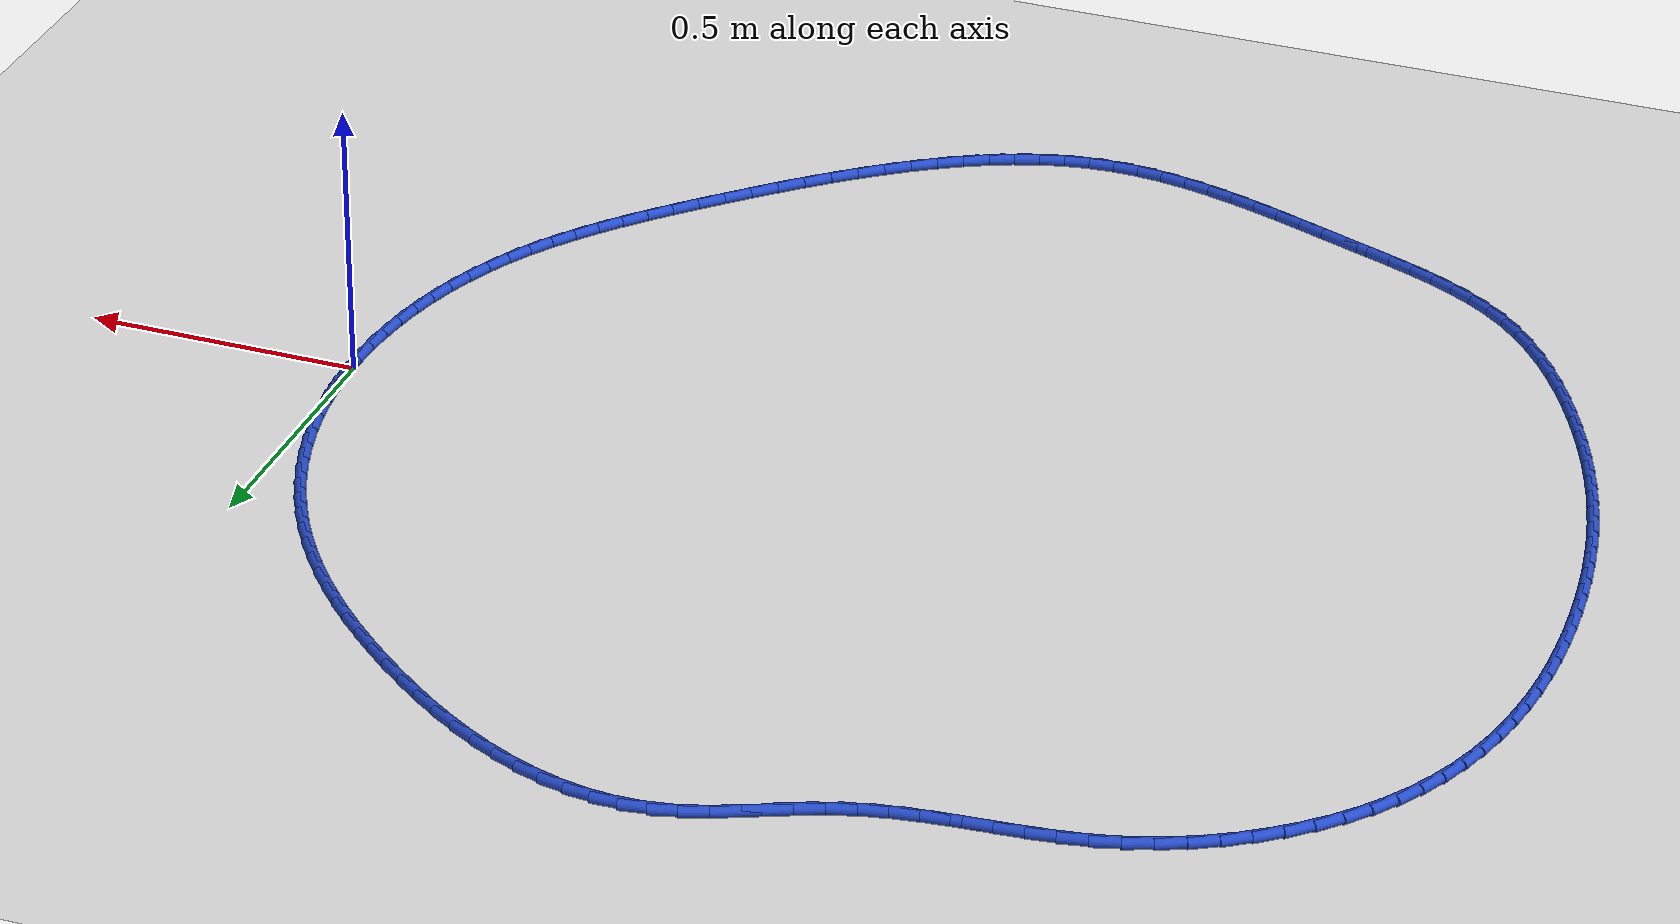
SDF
<sdf version="1.6">
 <world name="default">
  <light name="sun" type="directional">
   <pose>0 0 10 0 -0 0</pose>
   <diffuse>0.8 0.8 0.8 1</diffuse>
   <specular>0.2 0.2 0.2 1</specular>
   <attenuation>
    <range>1000</range>
    <constant>0.9</constant>
    <linear>0.01</linear>
    <quadratic>0.001</quadratic>
   </attenuation>
   <direction>-0.5 0.1 -0.9</direction>
  </light>
  <model name="ground_plane">
   <static>1</static>
   <link name="link">
    <collision name="collision">
     <geometry><plane><normal>0 0 1</normal><size>100 100</size></plane></geometry>
     <surface><friction><ode><mu>100</mu><mu2>50</mu2></ode></friction></surface>
    </collision>
    <visual name="visual">
     <cast_shadows>0</cast_shadows>
     <geometry><plane><normal>0 0 1</normal><size>100 100</size></plane></geometry>
     <material>
      <script><uri>file://media/materials/scripts/gazebo.material</uri><name>Gazebo/WhiteGlow</name></script>
     </material>
    </visual>
   </link>
  </model>
  <gravity>0 0 -9.8</gravity>
  <magnetic_field>6e-06 2.3e-05 -4.2e-05</magnetic_field>
  <atmosphere type="adiabatic"/>
  <physics name="default_physics" default="0" type="ode">
   <max_step_size>0.001</max_step_size>
   <real_time_factor>1</real_time_factor>
   <real_time_update_rate>1000</real_time_update_rate>
  </physics>
  <scene><ambient>0.4 0.4 0.4 1</ambient><background>0.7 0.7 0.7 1</background><shadows>1</shadows></scene>
  <spherical_coordinates>
   <surface_model>EARTH_WGS84</surface_model>
   <latitude_deg>0</latitude_deg>
   <longitude_deg>0</longitude_deg>
   <elevation>0</elevation>
   <heading_deg>0</heading_deg>
  </spherical_coordinates>
  <model name="line">
   <link name="link_0">
    <pose>2.2551405187698492e-17 5.551115123125783e-17 0.01 0 1.57 -1.5392419877044776</pose>
    <collision name="collision">
     <geometry><cylinder><radius>0.01</radius><length>0.08</length></cylinder></geometry>
    </collision>
    <visual name="visual">
     <material>
      <script><name>Gazebo/Blue</name><uri>file://media/materials/scripts/gazebo.material</uri></script>
     </material>
     <geometry><cylinder><radius>0.01</radius><length>0.08</length></cylinder></geometry>
    </visual>
   </link>
   <link name="link_1">
    <pose>-0.0015824500909776397 0.05013335404957283 0.01 0 1.57 -1.4899112611273708</pose>
    <collision name="collision">
     <geometry><cylinder><radius>0.01</radius><length>0.08</length></cylinder></geometry>
    </collision>
    <visual name="visual">
     <material>
      <script><name>Gazebo/Blue</name><uri>file://media/materials/scripts/gazebo.material</uri></script>
     </material>
     <geometry><cylinder><radius>0.01</radius><length>0.08</length></cylinder></geometry>
    </visual>
   </link>
   <link name="link_2">
    <pose>-0.005628785693399329 0.10004995456834834 0.01 0 1.57 -1.441327607142462</pose>
    <collision name="collision">
     <geometry><cylinder><radius>0.01</radius><length>0.08</length></cylinder></geometry>
    </collision>
    <visual name="visual">
     <material>
      <script><name>Gazebo/Blue</name><uri>file://media/materials/scripts/gazebo.material</uri></script>
     </material>
     <geometry><cylinder><radius>0.01</radius><length>0.08</length></cylinder></geometry>
    </visual>
   </link>
   <link name="link_3">
    <pose>-0.012081902913729146 0.14961421103972397 0.01 0 1.57 -1.393314175987291</pose>
    <collision name="collision">
     <geometry><cylinder><radius>0.01</radius><length>0.08</length></cylinder></geometry>
    </collision>
    <visual name="visual">
     <material>
      <script><name>Gazebo/Blue</name><uri>file://media/materials/scripts/gazebo.material</uri></script>
     </material>
     <geometry><cylinder><radius>0.01</radius><length>0.08</length></cylinder></geometry>
    </visual>
   </link>
   <link name="link_4">
    <pose>-0.020884697858431205 0.19869053294709701 0.01 0 1.57 -1.3456842124285278</pose>
    <collision name="collision">
     <geometry><cylinder><radius>0.01</radius><length>0.08</length></cylinder></geometry>
    </collision>
    <visual name="visual">
     <material>
      <script><name>Gazebo/Blue</name><uri>file://media/materials/scripts/gazebo.material</uri></script>
     </material>
     <geometry><cylinder><radius>0.01</radius><length>0.08</length></cylinder></geometry>
    </visual>
   </link>
   <link name="link_5">
    <pose>-0.031980066633969635 0.24714332977386483 0.01 0 1.57 -1.2982424886802975</pose>
    <collision name="collision">
     <geometry><cylinder><radius>0.01</radius><length>0.08</length></cylinder></geometry>
    </collision>
    <visual name="visual">
     <material>
      <script><name>Gazebo/Blue</name><uri>file://media/materials/scripts/gazebo.material</uri></script>
     </material>
     <geometry><cylinder><radius>0.01</radius><length>0.08</length></cylinder></geometry>
    </visual>
   </link>
   <link name="link_6">
    <pose>-0.04531090534680854 0.29483701100342474 0.01 0 1.57 -1.2507863105780639</pose>
    <collision name="collision">
     <geometry><cylinder><radius>0.01</radius><length>0.08</length></cylinder></geometry>
    </collision>
    <visual name="visual">
     <material>
      <script><name>Gazebo/Blue</name><uri>file://media/materials/scripts/gazebo.material</uri></script>
     </material>
     <geometry><cylinder><radius>0.01</radius><length>0.08</length></cylinder></geometry>
    </visual>
   </link>
   <link name="link_7">
    <pose>-0.06082011010341201 0.3416359861191741 0.01 0 1.57 -1.2031062376416208</pose>
    <collision name="collision">
     <geometry><cylinder><radius>0.01</radius><length>0.08</length></cylinder></geometry>
    </collision>
    <visual name="visual">
     <material>
      <script><name>Gazebo/Blue</name><uri>file://media/materials/scripts/gazebo.material</uri></script>
     </material>
     <geometry><cylinder><radius>0.01</radius><length>0.08</length></cylinder></geometry>
    </visual>
   </link>
   <link name="link_8">
    <pose>-0.07845057701024422 0.3874046646045103 0.01 0 1.57 -1.1549866741841799</pose>
    <collision name="collision">
     <geometry><cylinder><radius>0.01</radius><length>0.08</length></cylinder></geometry>
    </collision>
    <visual name="visual">
     <material>
      <script><name>Gazebo/Blue</name><uri>file://media/materials/scripts/gazebo.material</uri></script>
     </material>
     <geometry><cylinder><radius>0.01</radius><length>0.08</length></cylinder></geometry>
    </visual>
   </link>
   <link name="link_9">
    <pose>-0.09814520217376921 0.43200745594283047 0.01 0 1.57 -1.1064393421343046</pose>
    <collision name="collision">
     <geometry><cylinder><radius>0.01</radius><length>0.08</length></cylinder></geometry>
    </collision>
    <visual name="visual">
     <material>
      <script><name>Gazebo/Blue</name><uri>file://media/materials/scripts/gazebo.material</uri></script>
     </material>
     <geometry><cylinder><radius>0.01</radius><length>0.08</length></cylinder></geometry>
    </visual>
   </link>
   <link name="link_10">
    <pose>-0.11984924948275016 0.4753386779965507 0.01 0 1.57 -1.0585171125424098</pose>
    <collision name="collision">
     <geometry><cylinder><radius>0.01</radius><length>0.08</length></cylinder></geometry>
    </collision>
    <visual name="visual">
     <material>
      <script><name>Gazebo/Blue</name><uri>file://media/materials/scripts/gazebo.material</uri></script>
     </material>
     <geometry><cylinder><radius>0.01</radius><length>0.08</length></cylinder></geometry>
    </visual>
   </link>
   <link name="link_11">
    <pose>-0.14351874961716266 0.5174286481549553 0.01 0 1.57 -1.0118368616197726</pose>
    <collision name="collision">
     <geometry><cylinder><radius>0.01</radius><length>0.08</length></cylinder></geometry>
    </collision>
    <visual name="visual">
     <material>
      <script><name>Gazebo/Blue</name><uri>file://media/materials/scripts/gazebo.material</uri></script>
     </material>
     <geometry><cylinder><radius>0.01</radius><length>0.08</length></cylinder></geometry>
    </visual>
   </link>
   <link name="link_12">
    <pose>-0.1691127919916613 0.5583463198745606 0.01 0 1.57 -0.966714887193477</pose>
    <collision name="collision">
     <geometry><cylinder><radius>0.01</radius><length>0.08</length></cylinder></geometry>
    </collision>
    <visual name="visual">
     <material>
      <script><name>Gazebo/Blue</name><uri>file://media/materials/scripts/gazebo.material</uri></script>
     </material>
     <geometry><cylinder><radius>0.01</radius><length>0.08</length></cylinder></geometry>
    </visual>
   </link>
   <link name="link_13">
    <pose>-0.1965904662309409 0.5981606492649827 0.01 0 1.57 -0.9234209997527437</pose>
    <collision name="collision">
     <geometry><cylinder><radius>0.01</radius><length>0.08</length></cylinder></geometry>
    </collision>
    <visual name="visual">
     <material>
      <script><name>Gazebo/Blue</name><uri>file://media/materials/scripts/gazebo.material</uri></script>
     </material>
     <geometry><cylinder><radius>0.01</radius><length>0.08</length></cylinder></geometry>
    </visual>
   </link>
   <link name="link_14">
    <pose>-0.22591086195969612 0.6369405924358381 0.01 0 1.57 -0.8821738849087701</pose>
    <collision name="collision">
     <geometry><cylinder><radius>0.01</radius><length>0.08</length></cylinder></geometry>
    </collision>
    <visual name="visual">
     <material>
      <script><name>Gazebo/Blue</name><uri>file://media/materials/scripts/gazebo.material</uri></script>
     </material>
     <geometry><cylinder><radius>0.01</radius><length>0.08</length></cylinder></geometry>
    </visual>
   </link>
   <link name="link_15">
    <pose>-0.2570330688026219 0.6747551054967431 0.01 0 1.57 -0.8431399966090858</pose>
    <collision name="collision">
     <geometry><cylinder><radius>0.01</radius><length>0.08</length></cylinder></geometry>
    </collision>
    <visual name="visual">
     <material>
      <script><name>Gazebo/Blue</name><uri>file://media/materials/scripts/gazebo.material</uri></script>
     </material>
     <geometry><cylinder><radius>0.01</radius><length>0.08</length></cylinder></geometry>
    </visual>
   </link>
   <link name="link_16">
    <pose>-0.2899161763844131 0.7116731445573139 0.01 0 1.57 -0.806435476350646</pose>
    <collision name="collision">
     <geometry><cylinder><radius>0.01</radius><length>0.08</length></cylinder></geometry>
    </collision>
    <visual name="visual">
     <material>
      <script><name>Gazebo/Blue</name><uri>file://media/materials/scripts/gazebo.material</uri></script>
     </material>
     <geometry><cylinder><radius>0.01</radius><length>0.08</length></cylinder></geometry>
    </visual>
   </link>
   <link name="link_17">
    <pose>-0.3245192743297643 0.7477636657271667 0.01 0 1.57 -0.7721303531220928</pose>
    <collision name="collision">
     <geometry><cylinder><radius>0.01</radius><length>0.08</length></cylinder></geometry>
    </collision>
    <visual name="visual">
     <material>
      <script><name>Gazebo/Blue</name><uri>file://media/materials/scripts/gazebo.material</uri></script>
     </material>
     <geometry><cylinder><radius>0.01</radius><length>0.08</length></cylinder></geometry>
    </visual>
   </link>
   <link name="link_18">
    <pose>-0.36080145226337046 0.7830956251159183 0.01 0 1.57 -0.7402542169141524</pose>
    <collision name="collision">
     <geometry><cylinder><radius>0.01</radius><length>0.08</length></cylinder></geometry>
    </collision>
    <visual name="visual">
     <material>
      <script><name>Gazebo/Blue</name><uri>file://media/materials/scripts/gazebo.material</uri></script>
     </material>
     <geometry><cylinder><radius>0.01</radius><length>0.08</length></cylinder></geometry>
    </visual>
   </link>
   <link name="link_19">
    <pose>-0.39872179980992656 0.8177379788331848 0.01 0 1.57 -0.7108026198623999</pose>
    <collision name="collision">
     <geometry><cylinder><radius>0.01</radius><length>0.08</length></cylinder></geometry>
    </collision>
    <visual name="visual">
     <material>
      <script><name>Gazebo/Blue</name><uri>file://media/materials/scripts/gazebo.material</uri></script>
     </material>
     <geometry><cylinder><radius>0.01</radius><length>0.08</length></cylinder></geometry>
    </visual>
   </link>
   <link name="link_20">
    <pose>-0.4382394065941272 0.8517596829885825 0.01 0 1.57 -0.6835301239907299</pose>
    <collision name="collision">
     <geometry><cylinder><radius>0.01</radius><length>0.08</length></cylinder></geometry>
    </collision>
    <visual name="visual">
     <material>
      <script><name>Gazebo/Blue</name><uri>file://media/materials/scripts/gazebo.material</uri></script>
     </material>
     <geometry><cylinder><radius>0.01</radius><length>0.08</length></cylinder></geometry>
    </visual>
   </link>
   <link name="link_21">
    <pose>-0.4793087480708249 0.8852113476380054 0.01 0 1.57 -0.6549149466255842</pose>
    <collision name="collision">
     <geometry><cylinder><radius>0.01</radius><length>0.08</length></cylinder></geometry>
    </collision>
    <visual name="visual">
     <material>
      <script><name>Gazebo/Blue</name><uri>file://media/materials/scripts/gazebo.material</uri></script>
     </material>
     <geometry><cylinder><radius>0.01</radius><length>0.08</length></cylinder></geometry>
    </visual>
   </link>
   <link name="link_22">
    <pose>-0.5218111445369205 0.9178527161151081 0.01 0 1.57 -0.6217961569317273</pose>
    <collision name="collision">
     <geometry><cylinder><radius>0.01</radius><length>0.08</length></cylinder></geometry>
    </collision>
    <visual name="visual">
     <material>
      <script><name>Gazebo/Blue</name><uri>file://media/materials/scripts/gazebo.material</uri></script>
     </material>
     <geometry><cylinder><radius>0.01</radius><length>0.08</length></cylinder></geometry>
    </visual>
   </link>
   <link name="link_23">
    <pose>-0.565569420404114 0.9492109506633142 0.01 0 1.57 -0.5834418346859622</pose>
    <collision name="collision">
     <geometry><cylinder><radius>0.01</radius><length>0.08</length></cylinder></geometry>
    </collision>
    <visual name="visual">
     <material>
      <script><name>Gazebo/Blue</name><uri>file://media/materials/scripts/gazebo.material</uri></script>
     </material>
     <geometry><cylinder><radius>0.01</radius><length>0.08</length></cylinder></geometry>
    </visual>
   </link>
   <link name="link_24">
    <pose>-0.6104047638069376 0.9788067076474446 0.01 0 1.57 -0.5390320632942563</pose>
    <collision name="collision">
     <geometry><cylinder><radius>0.01</radius><length>0.08</length></cylinder></geometry>
    </collision>
    <visual name="visual">
     <material>
      <script><name>Gazebo/Blue</name><uri>file://media/materials/scripts/gazebo.material</uri></script>
     </material>
     <geometry><cylinder><radius>0.01</radius><length>0.08</length></cylinder></geometry>
    </visual>
   </link>
   <link name="link_25">
    <pose>-0.6561383628799232 1.0061606434323216 0.01 0 1.57 -0.48757129271276384</pose>
    <collision name="collision">
     <geometry><cylinder><radius>0.01</radius><length>0.08</length></cylinder></geometry>
    </collision>
    <visual name="visual">
     <material>
      <script><name>Gazebo/Blue</name><uri>file://media/materials/scripts/gazebo.material</uri></script>
     </material>
     <geometry><cylinder><radius>0.01</radius><length>0.08</length></cylinder></geometry>
    </visual>
   </link>
   <link name="link_26">
    <pose>-0.7025914057576026 1.0307934143827664 0.01 0 1.57 -0.4278877450155994</pose>
    <collision name="collision">
     <geometry><cylinder><radius>0.01</radius><length>0.08</length></cylinder></geometry>
    </collision>
    <visual name="visual">
     <material>
      <script><name>Gazebo/Blue</name><uri>file://media/materials/scripts/gazebo.material</uri></script>
     </material>
     <geometry><cylinder><radius>0.01</radius><length>0.08</length></cylinder></geometry>
    </visual>
   </link>
   <link name="link_27">
    <pose>-0.7495850805745078 1.0522256768636007 0.01 0 1.57 -0.3586614327481904</pose>
    <collision name="collision">
     <geometry><cylinder><radius>0.01</radius><length>0.08</length></cylinder></geometry>
    </collision>
    <visual name="visual">
     <material>
      <script><name>Gazebo/Blue</name><uri>file://media/materials/scripts/gazebo.material</uri></script>
     </material>
     <geometry><cylinder><radius>0.01</radius><length>0.08</length></cylinder></geometry>
    </visual>
   </link>
   <link name="link_28">
    <pose>-0.79694057546517 1.0699780872396454 0.01 0 1.57 -0.27850939648362055</pose>
    <collision name="collision">
     <geometry><cylinder><radius>0.01</radius><length>0.08</length></cylinder></geometry>
    </collision>
    <visual name="visual">
     <material>
      <script><name>Gazebo/Blue</name><uri>file://media/materials/scripts/gazebo.material</uri></script>
     </material>
     <geometry><cylinder><radius>0.01</radius><length>0.08</length></cylinder></geometry>
    </visual>
   </link>
   <link name="link_29">
    <pose>-0.8444790785641223 1.0835713018757227 0.01 0 1.57 -0.18616911435305641</pose>
    <collision name="collision">
     <geometry><cylinder><radius>0.01</radius><length>0.08</length></cylinder></geometry>
    </collision>
    <visual name="visual">
     <material>
      <script><name>Gazebo/Blue</name><uri>file://media/materials/scripts/gazebo.material</uri></script>
     </material>
     <geometry><cylinder><radius>0.01</radius><length>0.08</length></cylinder></geometry>
    </visual>
   </link>
   <link name="link_30">
    <pose>-0.8920217780058954 1.0925259771366538 0.01 0 1.57 -0.08082307421567851</pose>
    <collision name="collision">
     <geometry><cylinder><radius>0.01</radius><length>0.08</length></cylinder></geometry>
    </collision>
    <visual name="visual">
     <material>
      <script><name>Gazebo/Blue</name><uri>file://media/materials/scripts/gazebo.material</uri></script>
     </material>
     <geometry><cylinder><radius>0.01</radius><length>0.08</length></cylinder></geometry>
    </visual>
   </link>
   <link name="link_31">
    <pose>-0.9393898619250219 1.0963627693872604 0.01 0 1.57 0.03742688895079316</pose>
    <collision name="collision">
     <geometry><cylinder><radius>0.01</radius><length>0.08</length></cylinder></geometry>
    </collision>
    <visual name="visual">
     <material>
      <script><name>Gazebo/Blue</name><uri>file://media/materials/scripts/gazebo.material</uri></script>
     </material>
     <geometry><cylinder><radius>0.01</radius><length>0.08</length></cylinder></geometry>
    </visual>
   </link>
   <link name="link_32">
    <pose>-0.9864045184560334 1.094602334992364 0.01 0 1.57 0.16702672020948092</pose>
    <collision name="collision">
     <geometry><cylinder><radius>0.01</radius><length>0.08</length></cylinder></geometry>
    </collision>
    <visual name="visual">
     <material>
      <script><name>Gazebo/Blue</name><uri>file://media/materials/scripts/gazebo.material</uri></script>
     </material>
     <geometry><cylinder><radius>0.01</radius><length>0.08</length></cylinder></geometry>
    </visual>
   </link>
   <link name="link_33">
    <pose>-1.0328869697737553 1.0867655106525285 0.01 0 1.57 0.29342911975674835</pose>
    <collision name="collision">
     <geometry><cylinder><radius>0.01</radius><length>0.08</length></cylinder></geometry>
    </collision>
    <visual name="visual">
     <material>
      <script><name>Gazebo/Blue</name><uri>file://media/materials/scripts/gazebo.material</uri></script>
     </material>
     <geometry><cylinder><radius>0.01</radius><length>0.08</length></cylinder></geometry>
    </visual>
   </link>
   <link name="link_34">
    <pose>-1.0787588829040953 1.0729052611754928 0.01 0 1.57 0.37911773989034736</pose>
    <collision name="collision">
     <geometry><cylinder><radius>0.01</radius><length>0.08</length></cylinder></geometry>
    </collision>
    <visual name="visual">
     <material>
      <script><name>Gazebo/Blue</name><uri>file://media/materials/scripts/gazebo.material</uri></script>
     </material>
     <geometry><cylinder><radius>0.01</radius><length>0.08</length></cylinder></geometry>
    </visual>
   </link>
   <link name="link_35">
    <pose>-1.1242632382312017 1.0547767776880896 0.01 0 1.57 0.42014440793725444</pose>
    <collision name="collision">
     <geometry><cylinder><radius>0.01</radius><length>0.08</length></cylinder></geometry>
    </collision>
    <visual name="visual">
     <material>
      <script><name>Gazebo/Blue</name><uri>file://media/materials/scripts/gazebo.material</uri></script>
     </material>
     <geometry><cylinder><radius>0.01</radius><length>0.08</length></cylinder></geometry>
    </visual>
   </link>
   <link name="link_36">
    <pose>-1.1697071305755533 1.034474911272627 0.01 0 1.57 0.4195668067032248</pose>
    <collision name="collision">
     <geometry><cylinder><radius>0.01</radius><length>0.08</length></cylinder></geometry>
    </collision>
    <visual name="visual">
     <material>
      <script><name>Gazebo/Blue</name><uri>file://media/materials/scripts/gazebo.material</uri></script>
     </material>
     <geometry><cylinder><radius>0.01</radius><length>0.08</length></cylinder></geometry>
    </visual>
   </link>
   <link name="link_37">
    <pose>-1.2153976547576284 1.0140945130114112 0.01 0 1.57 0.3780129767086306</pose>
    <collision name="collision">
     <geometry><cylinder><radius>0.01</radius><length>0.08</length></cylinder></geometry>
    </collision>
    <visual name="visual">
     <material>
      <script><name>Gazebo/Blue</name><uri>file://media/materials/scripts/gazebo.material</uri></script>
     </material>
     <geometry><cylinder><radius>0.01</radius><length>0.08</length></cylinder></geometry>
    </visual>
   </link>
   <link name="link_38">
    <pose>-1.2616419055979038 0.9957304339867483 0.01 0 1.57 0.2966278268644503</pose>
    <collision name="collision">
     <geometry><cylinder><radius>0.01</radius><length>0.08</length></cylinder></geometry>
    </collision>
    <visual name="visual">
     <material>
      <script><name>Gazebo/Blue</name><uri>file://media/materials/scripts/gazebo.material</uri></script>
     </material>
     <geometry><cylinder><radius>0.01</radius><length>0.08</length></cylinder></geometry>
    </visual>
   </link>
   <link name="link_39">
    <pose>-1.3087249159278107 0.9813397363183075 0.01 0 1.57 0.21031162187031924</pose>
    <collision name="collision">
     <geometry><cylinder><radius>0.01</radius><length>0.08</length></cylinder></geometry>
    </collision>
    <visual name="visual">
     <material>
      <script><name>Gazebo/Blue</name><uri>file://media/materials/scripts/gazebo.material</uri></script>
     </material>
     <geometry><cylinder><radius>0.01</radius><length>0.08</length></cylinder></geometry>
    </visual>
   </link>
   <link name="link_40">
    <pose>-1.356648336329136 0.9711096078808217 0.01 0 1.57 0.14534629082477085</pose>
    <collision name="collision">
     <geometry><cylinder><radius>0.01</radius><length>0.08</length></cylinder></geometry>
    </collision>
    <visual name="visual">
     <material>
      <script><name>Gazebo/Blue</name><uri>file://media/materials/scripts/gazebo.material</uri></script>
     </material>
     <geometry><cylinder><radius>0.01</radius><length>0.08</length></cylinder></geometry>
    </visual>
   </link>
   <link name="link_41">
    <pose>-1.4052173429932837 0.9640001485300259 0.01 0 1.57 0.10273306907359131</pose>
    <collision name="collision">
     <geometry><cylinder><radius>0.01</radius><length>0.08</length></cylinder></geometry>
    </collision>
    <visual name="visual">
     <material>
      <script><name>Gazebo/Blue</name><uri>file://media/materials/scripts/gazebo.material</uri></script>
     </material>
     <geometry><cylinder><radius>0.01</radius><length>0.08</length></cylinder></geometry>
    </visual>
   </link>
   <link name="link_42">
    <pose>-1.4542331659628833 0.958946812304601 0.01 0 1.57 0.0822629797242891</pose>
    <collision name="collision">
     <geometry><cylinder><radius>0.01</radius><length>0.08</length></cylinder></geometry>
    </collision>
    <visual name="visual">
     <material>
      <script><name>Gazebo/Blue</name><uri>file://media/materials/scripts/gazebo.material</uri></script>
     </material>
     <geometry><cylinder><radius>0.01</radius><length>0.08</length></cylinder></geometry>
    </visual>
   </link>
   <link name="link_43">
    <pose>-1.5034970352805643 0.954885053243228 0.01 0 1.57 0.08365070059474661</pose>
    <collision name="collision">
     <geometry><cylinder><radius>0.01</radius><length>0.08</length></cylinder></geometry>
    </collision>
    <visual name="visual">
     <material>
      <script><name>Gazebo/Blue</name><uri>file://media/materials/scripts/gazebo.material</uri></script>
     </material>
     <geometry><cylinder><radius>0.01</radius><length>0.08</length></cylinder></geometry>
    </visual>
   </link>
   <link name="link_44">
    <pose>-1.5528101809889567 0.9507503253845875 0.01 0 1.57 0.10683035589574404</pose>
    <collision name="collision">
     <geometry><cylinder><radius>0.01</radius><length>0.08</length></cylinder></geometry>
    </collision>
    <visual name="visual">
     <material>
      <script><name>Gazebo/Blue</name><uri>file://media/materials/scripts/gazebo.material</uri></script>
     </material>
     <geometry><cylinder><radius>0.01</radius><length>0.08</length></cylinder></geometry>
    </visual>
   </link>
   <link name="link_45">
    <pose>-1.60197383313069 0.9454780827673612 0.01 0 1.57 0.15193370260324243</pose>
    <collision name="collision">
     <geometry><cylinder><radius>0.01</radius><length>0.08</length></cylinder></geometry>
    </collision>
    <visual name="visual">
     <material>
      <script><name>Gazebo/Blue</name><uri>file://media/materials/scripts/gazebo.material</uri></script>
     </material>
     <geometry><cylinder><radius>0.01</radius><length>0.08</length></cylinder></geometry>
    </visual>
   </link>
   <link name="link_46">
    <pose>-1.6507892217483935 0.9380037794302294 0.01 0 1.57 0.21895414129044602</pose>
    <collision name="collision">
     <geometry><cylinder><radius>0.01</radius><length>0.08</length></cylinder></geometry>
    </collision>
    <visual name="visual">
     <material>
      <script><name>Gazebo/Blue</name><uri>file://media/materials/scripts/gazebo.material</uri></script>
     </material>
     <geometry><cylinder><radius>0.01</radius><length>0.08</length></cylinder></geometry>
    </visual>
   </link>
   <link name="link_47">
    <pose>-1.6990575642791026 0.9272630344660207 0.01 0 1.57 0.3018115379057464</pose>
    <collision name="collision">
     <geometry><cylinder><radius>0.01</radius><length>0.08</length></cylinder></geometry>
    </collision>
    <visual name="visual">
     <material>
      <script><name>Gazebo/Blue</name><uri>file://media/materials/scripts/gazebo.material</uri></script>
     </material>
     <geometry><cylinder><radius>0.01</radius><length>0.08</length></cylinder></geometry>
    </visual>
   </link>
   <link name="link_48">
    <pose>-1.7465584271621464 0.9124749591137049 0.01 0 1.57 0.383708277931787</pose>
    <collision name="collision">
     <geometry><cylinder><radius>0.01</radius><length>0.08</length></cylinder></geometry>
    </collision>
    <visual name="visual">
     <material>
      <script><name>Gazebo/Blue</name><uri>file://media/materials/scripts/gazebo.material</uri></script>
     </material>
     <geometry><cylinder><radius>0.01</radius><length>0.08</length></cylinder></geometry>
    </visual>
   </link>
   <link name="link_49">
    <pose>-1.7930053300549247 0.8937234628173152 0.01 0 1.57 0.4622226124392185</pose>
    <collision name="collision">
     <geometry><cylinder><radius>0.01</radius><length>0.08</length></cylinder></geometry>
    </collision>
    <visual name="visual">
     <material>
      <script><name>Gazebo/Blue</name><uri>file://media/materials/scripts/gazebo.material</uri></script>
     </material>
     <geometry><cylinder><radius>0.01</radius><length>0.08</length></cylinder></geometry>
    </visual>
   </link>
   <link name="link_50">
    <pose>-1.8380992432890912 0.8712567724041635 0.01 0 1.57 0.5381911312860926</pose>
    <collision name="collision">
     <geometry><cylinder><radius>0.01</radius><length>0.08</length></cylinder></geometry>
    </collision>
    <visual name="visual">
     <material>
      <script><name>Gazebo/Blue</name><uri>file://media/materials/scripts/gazebo.material</uri></script>
     </material>
     <geometry><cylinder><radius>0.01</radius><length>0.08</length></cylinder></geometry>
    </visual>
   </link>
   <link name="link_51">
    <pose>-1.8815411371962982 0.8453231147015619 0.01 0 1.57 0.6124838152362039</pose>
    <collision name="collision">
     <geometry><cylinder><radius>0.01</radius><length>0.08</length></cylinder></geometry>
    </collision>
    <visual name="visual">
     <material>
      <script><name>Gazebo/Blue</name><uri>file://media/materials/scripts/gazebo.material</uri></script>
     </material>
     <geometry><cylinder><radius>0.01</radius><length>0.08</length></cylinder></geometry>
    </visual>
   </link>
   <link name="link_52">
    <pose>-1.9230319821082007 0.8161707165368227 0.01 0 1.57 0.6859863716296386</pose>
    <collision name="collision">
     <geometry><cylinder><radius>0.01</radius><length>0.08</length></cylinder></geometry>
    </collision>
    <visual name="visual">
     <material>
      <script><name>Gazebo/Blue</name><uri>file://media/materials/scripts/gazebo.material</uri></script>
     </material>
     <geometry><cylinder><radius>0.01</radius><length>0.08</length></cylinder></geometry>
    </visual>
   </link>
   <link name="link_53">
    <pose>-1.9622727483564508 0.7840478047372582 0.01 0 1.57 0.7595925925161336</pose>
    <collision name="collision">
     <geometry><cylinder><radius>0.01</radius><length>0.08</length></cylinder></geometry>
    </collision>
    <visual name="visual">
     <material>
      <script><name>Gazebo/Blue</name><uri>file://media/materials/scripts/gazebo.material</uri></script>
     </material>
     <geometry><cylinder><radius>0.01</radius><length>0.08</length></cylinder></geometry>
    </visual>
   </link>
   <link name="link_54">
    <pose>-1.998964406272702 0.7492026061301803 0.01 0 1.57 0.8342014682254628</pose>
    <collision name="collision">
     <geometry><cylinder><radius>0.01</radius><length>0.08</length></cylinder></geometry>
    </collision>
    <visual name="visual">
     <material>
      <script><name>Gazebo/Blue</name><uri>file://media/materials/scripts/gazebo.material</uri></script>
     </material>
     <geometry><cylinder><radius>0.01</radius><length>0.08</length></cylinder></geometry>
    </visual>
   </link>
   <link name="link_55">
    <pose>-2.032807926188609 0.7118833475429014 0.01 0 1.57 0.9107140737216107</pose>
    <collision name="collision">
     <geometry><cylinder><radius>0.01</radius><length>0.08</length></cylinder></geometry>
    </collision>
    <visual name="visual">
     <material>
      <script><name>Gazebo/Blue</name><uri>file://media/materials/scripts/gazebo.material</uri></script>
     </material>
     <geometry><cylinder><radius>0.01</radius><length>0.08</length></cylinder></geometry>
    </visual>
   </link>
   <link name="link_56">
    <pose>-2.0635042784358237 0.6723382558027338 0.01 0 1.57 0.9899503967738145</pose>
    <collision name="collision">
     <geometry><cylinder><radius>0.01</radius><length>0.08</length></cylinder></geometry>
    </collision>
    <visual name="visual">
     <material>
      <script><name>Gazebo/Blue</name><uri>file://media/materials/scripts/gazebo.material</uri></script>
     </material>
     <geometry><cylinder><radius>0.01</radius><length>0.08</length></cylinder></geometry>
    </visual>
   </link>
   <link name="link_57">
    <pose>-2.0907592811038733 0.6308149324000812 0.01 0 1.57 1.0694534594975376</pose>
    <collision name="collision">
     <geometry><cylinder><radius>0.01</radius><length>0.08</length></cylinder></geometry>
    </collision>
    <visual name="visual">
     <material>
      <script><name>Gazebo/Blue</name><uri>file://media/materials/scripts/gazebo.material</uri></script>
     </material>
     <geometry><cylinder><radius>0.01</radius><length>0.08</length></cylinder></geometry>
    </visual>
   </link>
   <link name="link_58">
    <pose>-2.1144786287812 0.5875351957406681 0.01 0 1.57 1.1447221137645243</pose>
    <collision name="collision">
     <geometry><cylinder><radius>0.01</radius><length>0.08</length></cylinder></geometry>
    </collision>
    <visual name="visual">
     <material>
      <script><name>Gazebo/Blue</name><uri>file://media/materials/scripts/gazebo.material</uri></script>
     </material>
     <geometry><cylinder><radius>0.01</radius><length>0.08</length></cylinder></geometry>
    </visual>
   </link>
   <link name="link_59">
    <pose>-2.1348344695269077 0.542686493043836 0.01 0 1.57 1.2149536750144614</pose>
    <collision name="collision">
     <geometry><cylinder><radius>0.01</radius><length>0.08</length></cylinder></geometry>
    </collision>
    <visual name="visual">
     <material>
      <script><name>Gazebo/Blue</name><uri>file://media/materials/scripts/gazebo.material</uri></script>
     </material>
     <geometry><cylinder><radius>0.01</radius><length>0.08</length></cylinder></geometry>
    </visual>
   </link>
   <link name="link_60">
    <pose>-2.152017460521252 0.4964538839433895 0.01 0 1.57 1.279893554286889</pose>
    <collision name="collision">
     <geometry><cylinder><radius>0.01</radius><length>0.08</length></cylinder></geometry>
    </collision>
    <visual name="visual">
     <material>
      <script><name>Gazebo/Blue</name><uri>file://media/materials/scripts/gazebo.material</uri></script>
     </material>
     <geometry><cylinder><radius>0.01</radius><length>0.08</length></cylinder></geometry>
    </visual>
   </link>
   <link name="link_61">
    <pose>-2.1662182589444896 0.44902242807313303 0.01 0 1.57 1.3395026013068694</pose>
    <collision name="collision">
     <geometry><cylinder><radius>0.01</radius><length>0.08</length></cylinder></geometry>
    </collision>
    <visual name="visual">
     <material>
      <script><name>Gazebo/Blue</name><uri>file://media/materials/scripts/gazebo.material</uri></script>
     </material>
     <geometry><cylinder><radius>0.01</radius><length>0.08</length></cylinder></geometry>
    </visual>
   </link>
   <link name="link_62">
    <pose>-2.177627521976875 0.40057718506687157 0.01 0 1.57 1.3939013921778294</pose>
    <collision name="collision">
     <geometry><cylinder><radius>0.01</radius><length>0.08</length></cylinder></geometry>
    </collision>
    <visual name="visual">
     <material>
      <script><name>Gazebo/Blue</name><uri>file://media/materials/scripts/gazebo.material</uri></script>
     </material>
     <geometry><cylinder><radius>0.01</radius><length>0.08</length></cylinder></geometry>
    </visual>
   </link>
   <link name="link_63">
    <pose>-2.186435906798664 0.351303214558409 0.01 0 1.57 1.4433169912706783</pose>
    <collision name="collision">
     <geometry><cylinder><radius>0.01</radius><length>0.08</length></cylinder></geometry>
    </collision>
    <visual name="visual">
     <material>
      <script><name>Gazebo/Blue</name><uri>file://media/materials/scripts/gazebo.material</uri></script>
     </material>
     <geometry><cylinder><radius>0.01</radius><length>0.08</length></cylinder></geometry>
    </visual>
   </link>
   <link name="link_64">
    <pose>-2.192834070590114 0.30138557618155076 0.01 0 1.57 1.4880379596503301</pose>
    <collision name="collision">
     <geometry><cylinder><radius>0.01</radius><length>0.08</length></cylinder></geometry>
    </collision>
    <visual name="visual">
     <material>
      <script><name>Gazebo/Blue</name><uri>file://media/materials/scripts/gazebo.material</uri></script>
     </material>
     <geometry><cylinder><radius>0.01</radius><length>0.08</length></cylinder></geometry>
    </visual>
   </link>
   <link name="link_65">
    <pose>-2.19701267053148 0.25100932957010097 0.01 0 1.57 1.5283794942295408</pose>
    <collision name="collision">
     <geometry><cylinder><radius>0.01</radius><length>0.08</length></cylinder></geometry>
    </collision>
    <visual name="visual">
     <material>
      <script><name>Gazebo/Blue</name><uri>file://media/materials/scripts/gazebo.material</uri></script>
     </material>
     <geometry><cylinder><radius>0.01</radius><length>0.08</length></cylinder></geometry>
    </visual>
   </link>
   <link name="link_66">
    <pose>-2.1991623638030187 0.20035953435786402 0.01 0 1.57 1.5646581635604264</pose>
    <collision name="collision">
     <geometry><cylinder><radius>0.01</radius><length>0.08</length></cylinder></geometry>
    </collision>
    <visual name="visual">
     <material>
      <script><name>Gazebo/Blue</name><uri>file://media/materials/scripts/gazebo.material</uri></script>
     </material>
     <geometry><cylinder><radius>0.01</radius><length>0.08</length></cylinder></geometry>
    </visual>
   </link>
   <link name="link_67">
    <pose>-2.199473807584985 0.14962125017864505 0.01 0 1.57 -1.5444180998727453</pose>
    <collision name="collision">
     <geometry><cylinder><radius>0.01</radius><length>0.08</length></cylinder></geometry>
    </collision>
    <visual name="visual">
     <material>
      <script><name>Gazebo/Blue</name><uri>file://media/materials/scripts/gazebo.material</uri></script>
     </material>
     <geometry><cylinder><radius>0.01</radius><length>0.08</length></cylinder></geometry>
    </visual>
   </link>
   <link name="link_68">
    <pose>-2.198137659057635 0.09897953666624791 0.01 0 1.57 -1.5152948626477376</pose>
    <collision name="collision">
     <geometry><cylinder><radius>0.01</radius><length>0.08</length></cylinder></geometry>
    </collision>
    <visual name="visual">
     <material>
      <script><name>Gazebo/Blue</name><uri>file://media/materials/scripts/gazebo.material</uri></script>
     </material>
     <geometry><cylinder><radius>0.01</radius><length>0.08</length></cylinder></geometry>
    </visual>
   </link>
   <link name="link_69">
    <pose>-2.1953394785361056 0.048614977986031524 0.01 0 1.57 -1.4874704664132132</pose>
    <collision name="collision">
     <geometry><cylinder><radius>0.01</radius><length>0.08</length></cylinder></geometry>
    </collision>
    <visual name="visual">
     <material>
      <script><name>Gazebo/Blue</name><uri>file://media/materials/scripts/gazebo.material</uri></script>
     </material>
     <geometry><cylinder><radius>0.01</radius><length>0.08</length></cylinder></geometry>
    </visual>
   </link>
   <link name="link_70">
    <pose>-2.1911638966875233 -0.0013804662618174858 0.01 0 1.57 -1.4591810888252337</pose>
    <collision name="collision">
     <geometry><cylinder><radius>0.01</radius><length>0.08</length></cylinder></geometry>
    </collision>
    <visual name="visual">
     <material>
      <script><name>Gazebo/Blue</name><uri>file://media/materials/scripts/gazebo.material</uri></script>
     </material>
     <geometry><cylinder><radius>0.01</radius><length>0.08</length></cylinder></geometry>
    </visual>
   </link>
   <link name="link_71">
    <pose>-2.1856029158798402 -0.05099617177252678 0.01 0 1.57 -1.4303888919285477</pose>
    <collision name="collision">
     <geometry><cylinder><radius>0.01</radius><length>0.08</length></cylinder></geometry>
    </collision>
    <visual name="visual">
     <material>
      <script><name>Gazebo/Blue</name><uri>file://media/materials/scripts/gazebo.material</uri></script>
     </material>
     <geometry><cylinder><radius>0.01</radius><length>0.08</length></cylinder></geometry>
    </visual>
   </link>
   <link name="link_72">
    <pose>-2.17864510572064 -0.1002245284883883 0.01 0 1.57 -1.4011248757612391</pose>
    <collision name="collision">
     <geometry><cylinder><radius>0.01</radius><length>0.08</length></cylinder></geometry>
    </collision>
    <visual name="visual">
     <material>
      <script><name>Gazebo/Blue</name><uri>file://media/materials/scripts/gazebo.material</uri></script>
     </material>
     <geometry><cylinder><radius>0.01</radius><length>0.08</length></cylinder></geometry>
    </visual>
   </link>
   <link name="link_73">
    <pose>-2.170279035817502 -0.14905792635169432 0.01 0 1.57 -1.3714242217989658</pose>
    <collision name="collision">
     <geometry><cylinder><radius>0.01</radius><length>0.08</length></cylinder></geometry>
    </collision>
    <visual name="visual">
     <material>
      <script><name>Gazebo/Blue</name><uri>file://media/materials/scripts/gazebo.material</uri></script>
     </material>
     <geometry><cylinder><radius>0.01</radius><length>0.08</length></cylinder></geometry>
    </visual>
   </link>
   <link name="link_74">
    <pose>-2.1604932757780104 -0.19748875530473486 0.01 0 1.57 -1.341326187886954</pose>
    <collision name="collision">
     <geometry><cylinder><radius>0.01</radius><length>0.08</length></cylinder></geometry>
    </collision>
    <visual name="visual">
     <material>
      <script><name>Gazebo/Blue</name><uri>file://media/materials/scripts/gazebo.material</uri></script>
     </material>
     <geometry><cylinder><radius>0.01</radius><length>0.08</length></cylinder></geometry>
    </visual>
   </link>
   <link name="link_75">
    <pose>-2.1492763952097453 -0.24550940528980222 0.01 0 1.57 -1.3108739201133899</pose>
    <collision name="collision">
     <geometry><cylinder><radius>0.01</radius><length>0.08</length></cylinder></geometry>
    </collision>
    <visual name="visual">
     <material>
      <script><name>Gazebo/Blue</name><uri>file://media/materials/scripts/gazebo.material</uri></script>
     </material>
     <geometry><cylinder><radius>0.01</radius><length>0.08</length></cylinder></geometry>
    </visual>
   </link>
   <link name="link_76">
    <pose>-2.13661696372029 -0.293112266249188 0.01 0 1.57 -1.2801141792896633</pose>
    <collision name="collision">
     <geometry><cylinder><radius>0.01</radius><length>0.08</length></cylinder></geometry>
    </collision>
    <visual name="visual">
     <material>
      <script><name>Gazebo/Blue</name><uri>file://media/materials/scripts/gazebo.material</uri></script>
     </material>
     <geometry><cylinder><radius>0.01</radius><length>0.08</length></cylinder></geometry>
    </visual>
   </link>
   <link name="link_77">
    <pose>-2.1225035509172265 -0.34028972812518377 0.01 0 1.57 -1.2490969828201908</pose>
    <collision name="collision">
     <geometry><cylinder><radius>0.01</radius><length>0.08</length></cylinder></geometry>
    </collision>
    <visual name="visual">
     <material>
      <script><name>Gazebo/Blue</name><uri>file://media/materials/scripts/gazebo.material</uri></script>
     </material>
     <geometry><cylinder><radius>0.01</radius><length>0.08</length></cylinder></geometry>
    </visual>
   </link>
   <link name="link_78">
    <pose>-2.106924726408136 -0.3870341808600816 0.01 0 1.57 -1.2178751661548992</pose>
    <collision name="collision">
     <geometry><cylinder><radius>0.01</radius><length>0.08</length></cylinder></geometry>
    </collision>
    <visual name="visual">
     <material>
      <script><name>Gazebo/Blue</name><uri>file://media/materials/scripts/gazebo.material</uri></script>
     </material>
     <geometry><cylinder><radius>0.01</radius><length>0.08</length></cylinder></geometry>
    </visual>
   </link>
   <link name="link_79">
    <pose>-2.0898690598006024 -0.4333380143961719 0.01 0 1.57 -1.1865038715258132</pose>
    <collision name="collision">
     <geometry><cylinder><radius>0.01</radius><length>0.08</length></cylinder></geometry>
    </collision>
    <visual name="visual">
     <material>
      <script><name>Gazebo/Blue</name><uri>file://media/materials/scripts/gazebo.material</uri></script>
     </material>
     <geometry><cylinder><radius>0.01</radius><length>0.08</length></cylinder></geometry>
    </visual>
   </link>
   <link name="link_80">
    <pose>-2.0713251207022054 -0.47919361867574667 0.01 0 1.57 -1.1550399750461213</pose>
    <collision name="collision">
     <geometry><cylinder><radius>0.01</radius><length>0.08</length></cylinder></geometry>
    </collision>
    <visual name="visual">
     <material>
      <script><name>Gazebo/Blue</name><uri>file://media/materials/scripts/gazebo.material</uri></script>
     </material>
     <geometry><cylinder><radius>0.01</radius><length>0.08</length></cylinder></geometry>
    </visual>
   </link>
   <link name="link_81">
    <pose>-2.0512814787205285 -0.5245933836410976 0.01 0 1.57 -1.1235414662502141</pose>
    <collision name="collision">
     <geometry><cylinder><radius>0.01</radius><length>0.08</length></cylinder></geometry>
    </collision>
    <visual name="visual">
     <material>
      <script><name>Gazebo/Blue</name><uri>file://media/materials/scripts/gazebo.material</uri></script>
     </material>
     <geometry><cylinder><radius>0.01</radius><length>0.08</length></cylinder></geometry>
    </visual>
   </link>
   <link name="link_82">
    <pose>-2.0297267034631528 -0.5695296992345169 0.01 0 1.57 -1.0920606054845883</pose>
    <collision name="collision">
     <geometry><cylinder><radius>0.01</radius><length>0.08</length></cylinder></geometry>
    </collision>
    <visual name="visual">
     <material>
      <script><name>Gazebo/Blue</name><uri>file://media/materials/scripts/gazebo.material</uri></script>
     </material>
     <geometry><cylinder><radius>0.01</radius><length>0.08</length></cylinder></geometry>
    </visual>
   </link>
   <link name="link_83">
    <pose>-2.0066492350739775 -0.613994531556843 0.01 0 1.57 -1.0588065439045538</pose>
    <collision name="collision">
     <geometry><cylinder><radius>0.01</radius><length>0.08</length></cylinder></geometry>
    </collision>
    <visual name="visual">
     <material>
      <script><name>Gazebo/Blue</name><uri>file://media/materials/scripts/gazebo.material</uri></script>
     </material>
     <geometry><cylinder><radius>0.01</radius><length>0.08</length></cylinder></geometry>
    </visual>
   </link>
   <link name="link_84">
    <pose>-1.9819998768605247 -0.6578566302912489 0.01 0 1.57 -1.0191365488200446</pose>
    <collision name="collision">
     <geometry><cylinder><radius>0.01</radius><length>0.08</length></cylinder></geometry>
    </collision>
    <visual name="visual">
     <material>
      <script><name>Gazebo/Blue</name><uri>file://media/materials/scripts/gazebo.material</uri></script>
     </material>
     <geometry><cylinder><radius>0.01</radius><length>0.08</length></cylinder></geometry>
    </visual>
   </link>
   <link name="link_85">
    <pose>-1.9556397979138465 -0.7006912983778127 0.01 0 1.57 -0.9717755368665235</pose>
    <collision name="collision">
     <geometry><cylinder><radius>0.01</radius><length>0.08</length></cylinder></geometry>
    </collision>
    <visual name="visual">
     <material>
      <script><name>Gazebo/Blue</name><uri>file://media/materials/scripts/gazebo.material</uri></script>
     </material>
     <geometry><cylinder><radius>0.01</radius><length>0.08</length></cylinder></geometry>
    </visual>
   </link>
   <link name="link_86">
    <pose>-1.9274171103122404 -0.7420310923812079 0.01 0 1.57 -0.9159497588431387</pose>
    <collision name="collision">
     <geometry><cylinder><radius>0.01</radius><length>0.08</length></cylinder></geometry>
    </collision>
    <visual name="visual">
     <material>
      <script><name>Gazebo/Blue</name><uri>file://media/materials/scripts/gazebo.material</uri></script>
     </material>
     <geometry><cylinder><radius>0.01</radius><length>0.08</length></cylinder></geometry>
    </visual>
   </link>
   <link name="link_87">
    <pose>-1.8971799261340037 -0.7814085688661074 0.01 0 1.57 -0.8508282475264095</pose>
    <collision name="collision">
     <geometry><cylinder><radius>0.01</radius><length>0.08</length></cylinder></geometry>
    </collision>
    <visual name="visual">
     <material>
      <script><name>Gazebo/Blue</name><uri>file://media/materials/scripts/gazebo.material</uri></script>
     </material>
     <geometry><cylinder><radius>0.01</radius><length>0.08</length></cylinder></geometry>
    </visual>
   </link>
   <link name="link_88">
    <pose>-1.864776357457436 -0.8183562843971824 0.01 0 1.57 -0.7756368478321437</pose>
    <collision name="collision">
     <geometry><cylinder><radius>0.01</radius><length>0.08</length></cylinder></geometry>
    </collision>
    <visual name="visual">
     <material>
      <script><name>Gazebo/Blue</name><uri>file://media/materials/scripts/gazebo.material</uri></script>
     </material>
     <geometry><cylinder><radius>0.01</radius><length>0.08</length></cylinder></geometry>
    </visual>
   </link>
   <link name="link_89">
    <pose>-1.8300545163608346 -0.8524067955391063 0.01 0 1.57 -0.6899453912602648</pose>
    <collision name="collision">
     <geometry><cylinder><radius>0.01</radius><length>0.08</length></cylinder></geometry>
    </collision>
    <visual name="visual">
     <material>
      <script><name>Gazebo/Blue</name><uri>file://media/materials/scripts/gazebo.material</uri></script>
     </material>
     <geometry><cylinder><radius>0.01</radius><length>0.08</length></cylinder></geometry>
    </visual>
   </link>
   <link name="link_90">
    <pose>-1.792864707933202 -0.8830974730477348 0.01 0 1.57 -0.6019373760551543</pose>
    <collision name="collision">
     <geometry><cylinder><radius>0.01</radius><length>0.08</length></cylinder></geometry>
    </collision>
    <visual name="visual">
     <material>
      <script><name>Gazebo/Blue</name><uri>file://media/materials/scripts/gazebo.material</uri></script>
     </material>
     <geometry><cylinder><radius>0.01</radius><length>0.08</length></cylinder></geometry>
    </visual>
   </link>
   <link name="link_91">
    <pose>-1.7532233970017455 -0.9103304486649548 0.01 0 1.57 -0.5264662423646781</pose>
    <collision name="collision">
     <geometry><cylinder><radius>0.01</radius><length>0.08</length></cylinder></geometry>
    </collision>
    <visual name="visual">
     <material>
      <script><name>Gazebo/Blue</name><uri>file://media/materials/scripts/gazebo.material</uri></script>
     </material>
     <geometry><cylinder><radius>0.01</radius><length>0.08</length></cylinder></geometry>
    </visual>
   </link>
   <link name="link_92">
    <pose>-1.7114267330929145 -0.9346218299836897 0.01 0 1.57 -0.46566839820039385</pose>
    <collision name="collision">
     <geometry><cylinder><radius>0.01</radius><length>0.08</length></cylinder></geometry>
    </collision>
    <visual name="visual">
     <material>
      <script><name>Gazebo/Blue</name><uri>file://media/materials/scripts/gazebo.material</uri></script>
     </material>
     <geometry><cylinder><radius>0.01</radius><length>0.08</length></cylinder></geometry>
    </visual>
   </link>
   <link name="link_93">
    <pose>-1.667797711922012 -0.9565466585024128 0.01 0 1.57 -0.4195520862918084</pose>
    <collision name="collision">
     <geometry><cylinder><radius>0.01</radius><length>0.08</length></cylinder></geometry>
    </collision>
    <visual name="visual">
     <material>
      <script><name>Gazebo/Blue</name><uri>file://media/materials/scripts/gazebo.material</uri></script>
     </material>
     <geometry><cylinder><radius>0.01</radius><length>0.08</length></cylinder></geometry>
    </visual>
   </link>
   <link name="link_94">
    <pose>-1.6226593292043405 -0.976679975719597 0.01 0 1.57 -0.3876863857352821</pose>
    <collision name="collision">
     <geometry><cylinder><radius>0.01</radius><length>0.08</length></cylinder></geometry>
    </collision>
    <visual name="visual">
     <material>
      <script><name>Gazebo/Blue</name><uri>file://media/materials/scripts/gazebo.material</uri></script>
     </material>
     <geometry><cylinder><radius>0.01</radius><length>0.08</length></cylinder></geometry>
    </visual>
   </link>
   <link name="link_95">
    <pose>-1.576334580655202 -0.9955968231337151 0.01 0 1.57 -0.3695004505435036</pose>
    <collision name="collision">
     <geometry><cylinder><radius>0.01</radius><length>0.08</length></cylinder></geometry>
    </collision>
    <visual name="visual">
     <material>
      <script><name>Gazebo/Blue</name><uri>file://media/materials/scripts/gazebo.material</uri></script>
     </material>
     <geometry><cylinder><radius>0.01</radius><length>0.08</length></cylinder></geometry>
    </visual>
   </link>
   <link name="link_96">
    <pose>-1.5291464619899005 -1.0138722422432398 0.01 0 1.57 -0.36446781154939983</pose>
    <collision name="collision">
     <geometry><cylinder><radius>0.01</radius><length>0.08</length></cylinder></geometry>
    </collision>
    <visual name="visual">
     <material>
      <script><name>Gazebo/Blue</name><uri>file://media/materials/scripts/gazebo.material</uri></script>
     </material>
     <geometry><cylinder><radius>0.01</radius><length>0.08</length></cylinder></geometry>
    </visual>
   </link>
   <link name="link_97">
    <pose>-1.481417963345396 -1.0320812508329937 0.01 0 1.57 -0.3681218276221707</pose>
    <collision name="collision">
     <geometry><cylinder><radius>0.01</radius><length>0.08</length></cylinder></geometry>
    </collision>
    <visual name="visual">
     <material>
      <script><name>Gazebo/Blue</name><uri>file://media/materials/scripts/gazebo.material</uri></script>
     </material>
     <geometry><cylinder><radius>0.01</radius><length>0.08</length></cylinder></geometry>
    </visual>
   </link>
   <link name="link_98">
    <pose>-1.433423615148575 -1.0505928634590882 0.01 0 1.57 -0.3663790103285619</pose>
    <collision name="collision">
     <geometry><cylinder><radius>0.01</radius><length>0.08</length></cylinder></geometry>
    </collision>
    <visual name="visual">
     <material>
      <script><name>Gazebo/Blue</name><uri>file://media/materials/scripts/gazebo.material</uri></script>
     </material>
     <geometry><cylinder><radius>0.01</radius><length>0.08</length></cylinder></geometry>
    </visual>
   </link>
   <link name="link_99">
    <pose>-1.3852716004592005 -1.0690689485832288 0.01 0 1.57 -0.3562578978698484</pose>
    <collision name="collision">
     <geometry><cylinder><radius>0.01</radius><length>0.08</length></cylinder></geometry>
    </collision>
    <visual name="visual">
     <material>
      <script><name>Gazebo/Blue</name><uri>file://media/materials/scripts/gazebo.material</uri></script>
     </material>
     <geometry><cylinder><radius>0.01</radius><length>0.08</length></cylinder></geometry>
    </visual>
   </link>
   <link name="link_100">
    <pose>-1.33703443702805 -1.0870197607017713 0.01 0 1.57 -0.33756754620951596</pose>
    <collision name="collision">
     <geometry><cylinder><radius>0.01</radius><length>0.08</length></cylinder></geometry>
    </collision>
    <visual name="visual">
     <material>
      <script><name>Gazebo/Blue</name><uri>file://media/materials/scripts/gazebo.material</uri></script>
     </material>
     <geometry><cylinder><radius>0.01</radius><length>0.08</length></cylinder></geometry>
    </visual>
   </link>
   <link name="link_101">
    <pose>-1.2887846426059042 -1.1039555543110726 0.01 0 1.57 -0.3098960475349012</pose>
    <collision name="collision">
     <geometry><cylinder><radius>0.01</radius><length>0.08</length></cylinder></geometry>
    </collision>
    <visual name="visual">
     <material>
      <script><name>Gazebo/Blue</name><uri>file://media/materials/scripts/gazebo.material</uri></script>
     </material>
     <geometry><cylinder><radius>0.01</radius><length>0.08</length></cylinder></geometry>
    </visual>
   </link>
   <link name="link_102">
    <pose>-1.2405947349435407 -1.119386583907489 0.01 0 1.57 -0.27263083924705733</pose>
    <collision name="collision">
     <geometry><cylinder><radius>0.01</radius><length>0.08</length></cylinder></geometry>
    </collision>
    <visual name="visual">
     <material>
      <script><name>Gazebo/Blue</name><uri>file://media/materials/scripts/gazebo.material</uri></script>
     </material>
     <geometry><cylinder><radius>0.01</radius><length>0.08</length></cylinder></geometry>
    </visual>
   </link>
   <link name="link_103">
    <pose>-1.1925372317917378 -1.1328231039873775 0.01 0 1.57 -0.22499975958783147</pose>
    <collision name="collision">
     <geometry><cylinder><radius>0.01</radius><length>0.08</length></cylinder></geometry>
    </collision>
    <visual name="visual">
     <material>
      <script><name>Gazebo/Blue</name><uri>file://media/materials/scripts/gazebo.material</uri></script>
     </material>
     <geometry><cylinder><radius>0.01</radius><length>0.08</length></cylinder></geometry>
    </visual>
   </link>
   <link name="link_104">
    <pose>-1.1446846509012734 -1.1437753690470944 0.01 0 1.57 -0.16615214376609738</pose>
    <collision name="collision">
     <geometry><cylinder><radius>0.01</radius><length>0.08</length></cylinder></geometry>
    </collision>
    <visual name="visual">
     <material>
      <script><name>Gazebo/Blue</name><uri>file://media/materials/scripts/gazebo.material</uri></script>
     </material>
     <geometry><cylinder><radius>0.01</radius><length>0.08</length></cylinder></geometry>
    </visual>
   </link>
   <link name="link_105">
    <pose>-1.0971095100229273 -1.1517536335829959 0.01 0 1.57 -0.09530596029148143</pose>
    <collision name="collision">
     <geometry><cylinder><radius>0.01</radius><length>0.08</length></cylinder></geometry>
    </collision>
    <visual name="visual">
     <material>
      <script><name>Gazebo/Blue</name><uri>file://media/materials/scripts/gazebo.material</uri></script>
     </material>
     <geometry><cylinder><radius>0.01</radius><length>0.08</length></cylinder></geometry>
    </visual>
   </link>
   <link name="link_106">
    <pose>-1.0498843269074776 -1.1562681520914388 0.01 0 1.57 -0.011986488328204658</pose>
    <collision name="collision">
     <geometry><cylinder><radius>0.01</radius><length>0.08</length></cylinder></geometry>
    </collision>
    <visual name="visual">
     <material>
      <script><name>Gazebo/Blue</name><uri>file://media/materials/scripts/gazebo.material</uri></script>
     </material>
     <geometry><cylinder><radius>0.01</radius><length>0.08</length></cylinder></geometry>
    </visual>
   </link>
   <link name="link_107">
    <pose>-1.0030816193057022 -1.156829179068779 0.01 0 1.57 0.08319348826435806</pose>
    <collision name="collision">
     <geometry><cylinder><radius>0.01</radius><length>0.08</length></cylinder></geometry>
    </collision>
    <visual name="visual">
     <material>
      <script><name>Gazebo/Blue</name><uri>file://media/materials/scripts/gazebo.material</uri></script>
     </material>
     <geometry><cylinder><radius>0.01</radius><length>0.08</length></cylinder></geometry>
    </visual>
   </link>
   <link name="link_108">
    <pose>-0.9567725449705761 -1.152967652780672 0.01 0 1.57 0.180284974861105</pose>
    <collision name="collision">
     <geometry><cylinder><radius>0.01</radius><length>0.08</length></cylinder></geometry>
    </collision>
    <visual name="visual">
     <material>
      <script><name>Gazebo/Blue</name><uri>file://media/materials/scripts/gazebo.material</uri></script>
     </material>
     <geometry><cylinder><radius>0.01</radius><length>0.08</length></cylinder></geometry>
    </visual>
   </link>
   <link name="link_109">
    <pose>-0.9110012582879465 -1.1446251970204704 0.01 0 1.57 0.269812392289272</pose>
    <collision name="collision">
     <geometry><cylinder><radius>0.01</radius><length>0.08</length></cylinder></geometry>
    </collision>
    <visual name="visual">
     <material>
      <script><name>Gazebo/Blue</name><uri>file://media/materials/scripts/gazebo.material</uri></script>
     </material>
     <geometry><cylinder><radius>0.01</radius><length>0.08</length></cylinder></geometry>
    </visual>
   </link>
   <link name="link_110">
    <pose>-0.8657870919717991 -1.1321209404075274 0.01 0 1.57 0.3507612931226021</pose>
    <collision name="collision">
     <geometry><cylinder><radius>0.01</radius><length>0.08</length></cylinder></geometry>
    </collision>
    <visual name="visual">
     <material>
      <script><name>Gazebo/Blue</name><uri>file://media/materials/scripts/gazebo.material</uri></script>
     </material>
     <geometry><cylinder><radius>0.01</radius><length>0.08</length></cylinder></geometry>
    </visual>
   </link>
   <link name="link_111">
    <pose>-0.8211484560483648 -1.115788044422526 0.01 0 1.57 0.42300988790087635</pose>
    <collision name="collision">
     <geometry><cylinder><radius>0.01</radius><length>0.08</length></cylinder></geometry>
    </collision>
    <visual name="visual">
     <material>
      <script><name>Gazebo/Blue</name><uri>file://media/materials/scripts/gazebo.material</uri></script>
     </material>
     <geometry><cylinder><radius>0.01</radius><length>0.08</length></cylinder></geometry>
    </visual>
   </link>
   <link name="link_112">
    <pose>-0.7771037605438751 -1.0959596705461494 0.01 0 1.57 0.48684700243931867</pose>
    <collision name="collision">
     <geometry><cylinder><radius>0.01</radius><length>0.08</length></cylinder></geometry>
    </collision>
    <visual name="visual">
     <material>
      <script><name>Gazebo/Blue</name><uri>file://media/materials/scripts/gazebo.material</uri></script>
     </material>
     <geometry><cylinder><radius>0.01</radius><length>0.08</length></cylinder></geometry>
    </visual>
   </link>
   <link name="link_113">
    <pose>-0.7336714154845614 -1.0729689802590807 0.01 0 1.57 0.5428021710868159</pose>
    <collision name="collision">
     <geometry><cylinder><radius>0.01</radius><length>0.08</length></cylinder></geometry>
    </collision>
    <visual name="visual">
     <material>
      <script><name>Gazebo/Blue</name><uri>file://media/materials/scripts/gazebo.material</uri></script>
     </material>
     <geometry><cylinder><radius>0.01</radius><length>0.08</length></cylinder></geometry>
    </visual>
   </link>
   <link name="link_114">
    <pose>-0.6908698308966568 -1.0471491350420046 0.01 0 1.57 0.5915128387949321</pose>
    <collision name="collision">
     <geometry><cylinder><radius>0.01</radius><length>0.08</length></cylinder></geometry>
    </collision>
    <visual name="visual">
     <material>
      <script><name>Gazebo/Blue</name><uri>file://media/materials/scripts/gazebo.material</uri></script>
     </material>
     <geometry><cylinder><radius>0.01</radius><length>0.08</length></cylinder></geometry>
    </visual>
   </link>
   <link name="link_115">
    <pose>-0.648717416806392 -1.0188332963756026 0.01 0 1.57 0.6336332805074385</pose>
    <collision name="collision">
     <geometry><cylinder><radius>0.01</radius><length>0.08</length></cylinder></geometry>
    </collision>
    <visual name="visual">
     <material>
      <script><name>Gazebo/Blue</name><uri>file://media/materials/scripts/gazebo.material</uri></script>
     </material>
     <geometry><cylinder><radius>0.01</radius><length>0.08</length></cylinder></geometry>
    </visual>
   </link>
   <link name="link_116">
    <pose>-0.6072325832399994 -0.9883546257405594 0.01 0 1.57 0.6697784091779949</pose>
    <collision name="collision">
     <geometry><cylinder><radius>0.01</radius><length>0.08</length></cylinder></geometry>
    </collision>
    <visual name="visual">
     <material>
      <script><name>Gazebo/Blue</name><uri>file://media/materials/scripts/gazebo.material</uri></script>
     </material>
     <geometry><cylinder><radius>0.01</radius><length>0.08</length></cylinder></geometry>
    </visual>
   </link>
   <link name="link_117">
    <pose>-0.5664337402237096 -0.9560462846175573 0.01 0 1.57 0.7004924629686103</pose>
    <collision name="collision">
     <geometry><cylinder><radius>0.01</radius><length>0.08</length></cylinder></geometry>
    </collision>
    <visual name="visual">
     <material>
      <script><name>Gazebo/Blue</name><uri>file://media/materials/scripts/gazebo.material</uri></script>
     </material>
     <geometry><cylinder><radius>0.01</radius><length>0.08</length></cylinder></geometry>
    </visual>
   </link>
   <link name="link_118">
    <pose>-0.5263392977837558 -0.9222414344872801 0.01 0 1.57 0.7262334465762682</pose>
    <collision name="collision">
     <geometry><cylinder><radius>0.01</radius><length>0.08</length></cylinder></geometry>
    </collision>
    <visual name="visual">
     <material>
      <script><name>Gazebo/Blue</name><uri>file://media/materials/scripts/gazebo.material</uri></script>
     </material>
     <geometry><cylinder><radius>0.01</radius><length>0.08</length></cylinder></geometry>
    </visual>
   </link>
   <link name="link_119">
    <pose>-0.4869676659463692 -0.8872732368304118 0.01 0 1.57 0.7473663513151112</pose>
    <collision name="collision">
     <geometry><cylinder><radius>0.01</radius><length>0.08</length></cylinder></geometry>
    </collision>
    <visual name="visual">
     <material>
      <script><name>Gazebo/Blue</name><uri>file://media/materials/scripts/gazebo.material</uri></script>
     </material>
     <geometry><cylinder><radius>0.01</radius><length>0.08</length></cylinder></geometry>
    </visual>
   </link>
   <link name="link_120">
    <pose>-0.4483372547377814 -0.8514748531276348 0.01 0 1.57 0.7641602455984893</pose>
    <collision name="collision">
     <geometry><cylinder><radius>0.01</radius><length>0.08</length></cylinder></geometry>
    </collision>
    <visual name="visual">
     <material>
      <script><name>Gazebo/Blue</name><uri>file://media/materials/scripts/gazebo.material</uri></script>
     </material>
     <geometry><cylinder><radius>0.01</radius><length>0.08</length></cylinder></geometry>
    </visual>
   </link>
   <link name="link_121">
    <pose>-0.4104664741842243 -0.8151794448596327 0.01 0 1.57 0.7767868338883732</pose>
    <collision name="collision">
     <geometry><cylinder><radius>0.01</radius><length>0.08</length></cylinder></geometry>
    </collision>
    <visual name="visual">
     <material>
      <script><name>Gazebo/Blue</name><uri>file://media/materials/scripts/gazebo.material</uri></script>
     </material>
     <geometry><cylinder><radius>0.01</radius><length>0.08</length></cylinder></geometry>
    </visual>
   </link>
   <link name="link_122">
    <pose>-0.37337375133097145 -0.7787201185939948 0.01 0 1.57 0.7873433384116197</pose>
    <collision name="collision">
     <geometry><cylinder><radius>0.01</radius><length>0.08</length></cylinder></geometry>
    </collision>
    <visual name="visual">
     <material>
      <script><name>Gazebo/Blue</name><uri>file://media/materials/scripts/gazebo.material</uri></script>
     </material>
     <geometry><cylinder><radius>0.01</radius><length>0.08</length></cylinder></geometry>
    </visual>
   </link>
   <link name="link_123">
    <pose>-0.3371123984761992 -0.7423174212661101 0.01 0 1.57 0.8022087810713805</pose>
    <collision name="collision">
     <geometry><cylinder><radius>0.01</radius><length>0.08</length></cylinder></geometry>
    </collision>
    <visual name="visual">
     <material>
      <script><name>Gazebo/Blue</name><uri>file://media/materials/scripts/gazebo.material</uri></script>
     </material>
     <geometry><cylinder><radius>0.01</radius><length>0.08</length></cylinder></geometry>
    </visual>
   </link>
   <link name="link_124">
    <pose>-0.3018439264929014 -0.7058427897785157 0.01 0 1.57 0.8227833614549639</pose>
    <collision name="collision">
     <geometry><cylinder><radius>0.01</radius><length>0.08</length></cylinder></geometry>
    </collision>
    <visual name="visual">
     <material>
      <script><name>Gazebo/Blue</name><uri>file://media/materials/scripts/gazebo.material</uri></script>
     </material>
     <geometry><cylinder><radius>0.01</radius><length>0.08</length></cylinder></geometry>
    </visual>
   </link>
   <link name="link_125">
    <pose>-0.26775076049522706 -0.6691001798175797 0.01 0 1.57 0.8492384544215957</pose>
    <collision name="collision">
     <geometry><cylinder><radius>0.01</radius><length>0.08</length></cylinder></geometry>
    </collision>
    <visual name="visual">
     <material>
      <script><name>Gazebo/Blue</name><uri>file://media/materials/scripts/gazebo.material</uri></script>
     </material>
     <geometry><cylinder><radius>0.01</radius><length>0.08</length></cylinder></geometry>
    </visual>
   </link>
   <link name="link_126">
    <pose>-0.23501532559732438 -0.631893547069669 0.01 0 1.57 0.8816998466891066</pose>
    <collision name="collision">
     <geometry><cylinder><radius>0.01</radius><length>0.08</length></cylinder></geometry>
    </collision>
    <visual name="visual">
     <material>
      <script><name>Gazebo/Blue</name><uri>file://media/materials/scripts/gazebo.material</uri></script>
     </material>
     <geometry><cylinder><radius>0.01</radius><length>0.08</length></cylinder></geometry>
    </visual>
   </link>
   <link name="link_127">
    <pose>-0.2038200469133435 -0.5940268472211532 0.01 0 1.57 0.9202164643158062</pose>
    <collision name="collision">
     <geometry><cylinder><radius>0.01</radius><length>0.08</length></cylinder></geometry>
    </collision>
    <visual name="visual">
     <material>
      <script><name>Gazebo/Blue</name><uri>file://media/materials/scripts/gazebo.material</uri></script>
     </material>
     <geometry><cylinder><radius>0.01</radius><length>0.08</length></cylinder></geometry>
    </visual>
   </link>
   <link name="link_128">
    <pose>-0.17434734955743267 -0.5553040359583992 0.01 0 1.57 0.9647220140647708</pose>
    <collision name="collision">
     <geometry><cylinder><radius>0.01</radius><length>0.08</length></cylinder></geometry>
    </collision>
    <visual name="visual">
     <material>
      <script><name>Gazebo/Blue</name><uri>file://media/materials/scripts/gazebo.material</uri></script>
     </material>
     <geometry><cylinder><radius>0.01</radius><length>0.08</length></cylinder></geometry>
    </visual>
   </link>
   <link name="link_129">
    <pose>-0.14677965864374096 -0.5155290689677754 0.01 0 1.57 1.0149928726349755</pose>
    <collision name="collision">
     <geometry><cylinder><radius>0.01</radius><length>0.08</length></cylinder></geometry>
    </collision>
    <visual name="visual">
     <material>
      <script><name>Gazebo/Blue</name><uri>file://media/materials/scripts/gazebo.material</uri></script>
     </material>
     <geometry><cylinder><radius>0.01</radius><length>0.08</length></cylinder></geometry>
    </visual>
   </link>
   <link name="link_130">
    <pose>-0.12129939928641716 -0.4745059019356491 0.01 0 1.57 1.0706085552267577</pose>
    <collision name="collision">
     <geometry><cylinder><radius>0.01</radius><length>0.08</length></cylinder></geometry>
    </collision>
    <visual name="visual">
     <material>
      <script><name>Gazebo/Blue</name><uri>file://media/materials/scripts/gazebo.material</uri></script>
     </material>
     <geometry><cylinder><radius>0.01</radius><length>0.08</length></cylinder></geometry>
    </visual>
   </link>
   <link name="link_131">
    <pose>-0.09808899434316425 -0.43203849554841395 0.01 0 1.57 1.1296773356762617</pose>
    <collision name="collision">
     <geometry><cylinder><radius>0.01</radius><length>0.08</length></cylinder></geometry>
    </collision>
    <visual name="visual">
     <material>
      <script><name>Gazebo/Blue</name><uri>file://media/materials/scripts/gazebo.material</uri></script>
     </material>
     <geometry><cylinder><radius>0.01</radius><length>0.08</length></cylinder></geometry>
    </visual>
   </link>
   <link name="link_132">
    <pose>-0.07729800692951683 -0.38800362392363713 0.01 0 1.57 1.187449845624131</pose>
    <collision name="collision">
     <geometry><cylinder><radius>0.01</radius><length>0.08</length></cylinder></geometry>
    </collision>
    <visual name="visual">
     <material>
      <script><name>Gazebo/Blue</name><uri>file://media/materials/scripts/gazebo.material</uri></script>
     </material>
     <geometry><cylinder><radius>0.01</radius><length>0.08</length></cylinder></geometry>
    </visual>
   </link>
   <link name="link_133">
    <pose>-0.05896033338360957 -0.34253436553123423 0.01 0 1.57 1.2431907692703672</pose>
    <collision name="collision">
     <geometry><cylinder><radius>0.01</radius><length>0.08</length></cylinder></geometry>
    </collision>
    <visual name="visual">
     <material>
      <script><name>Gazebo/Blue</name><uri>file://media/materials/scripts/gazebo.material</uri></script>
     </material>
     <geometry><cylinder><radius>0.01</radius><length>0.08</length></cylinder></geometry>
    </visual>
   </link>
   <link name="link_134">
    <pose>-0.043084433147597405 -0.29582016409393286 0.01 0 1.57 1.2972024268148916</pose>
    <collision name="collision">
     <geometry><cylinder><radius>0.01</radius><length>0.08</length></cylinder></geometry>
    </collision>
    <visual name="visual">
     <material>
      <script><name>Gazebo/Blue</name><uri>file://media/materials/scripts/gazebo.material</uri></script>
     </material>
     <geometry><cylinder><radius>0.01</radius><length>0.08</length></cylinder></geometry>
    </visual>
   </link>
   <link name="link_135">
    <pose>-0.029678765663635136 -0.24805046333445988 0.01 0 1.57 1.3497963986366517</pose>
    <collision name="collision">
     <geometry><cylinder><radius>0.01</radius><length>0.08</length></cylinder></geometry>
    </collision>
    <visual name="visual">
     <material>
      <script><name>Gazebo/Blue</name><uri>file://media/materials/scripts/gazebo.material</uri></script>
     </material>
     <geometry><cylinder><radius>0.01</radius><length>0.08</length></cylinder></geometry>
    </visual>
   </link>
   <link name="link_136">
    <pose>-0.018751790373878138 -0.1994147069755443 0.01 0 1.57 1.4012884508622738</pose>
    <collision name="collision">
     <geometry><cylinder><radius>0.01</radius><length>0.08</length></cylinder></geometry>
    </collision>
    <visual name="visual">
     <material>
      <script><name>Gazebo/Blue</name><uri>file://media/materials/scripts/gazebo.material</uri></script>
     </material>
     <geometry><cylinder><radius>0.01</radius><length>0.08</length></cylinder></geometry>
    </visual>
   </link>
   <link name="link_137">
    <pose>-0.01031196672048115 -0.15010233873991308 0.01 0 1.57 1.4519955932619852</pose>
    <collision name="collision">
     <geometry><cylinder><radius>0.01</radius><length>0.08</length></cylinder></geometry>
    </collision>
    <visual name="visual">
     <material>
      <script><name>Gazebo/Blue</name><uri>file://media/materials/scripts/gazebo.material</uri></script>
     </material>
     <geometry><cylinder><radius>0.01</radius><length>0.08</length></cylinder></geometry>
    </visual>
   </link>
   <link name="link_138">
    <pose>-0.004367754145599144 -0.10030280235029362 0.01 0 1.57 1.502234693839077</pose>
    <collision name="collision">
     <geometry><cylinder><radius>0.01</radius><length>0.08</length></cylinder></geometry>
    </collision>
    <visual name="visual">
     <material>
      <script><name>Gazebo/Blue</name><uri>file://media/materials/scripts/gazebo.material</uri></script>
     </material>
     <geometry><cylinder><radius>0.01</radius><length>0.08</length></cylinder></geometry>
    </visual>
   </link>
   <link name="link_139">
    <pose>-0.0009276120913870936 -0.05020554152941361 0.01 0 1.57 1.5523221398672882</pose>
    <collision name="collision">
     <geometry><cylinder><radius>0.01</radius><length>0.08</length></cylinder></geometry>
    </collision>
    <visual name="visual">
     <material>
      <script><name>Gazebo/Blue</name><uri>file://media/materials/scripts/gazebo.material</uri></script>
     </material>
     <geometry><cylinder><radius>0.01</radius><length>0.08</length></cylinder></geometry>
    </visual>
   </link>
   <link name="link_140">
    <pose>3.642919299551295e-17 1.8041124150158794e-16 0.01 0 1.57 -1.5390185575791118</pose>
    <collision name="collision">
     <geometry><cylinder><radius>0.01</radius><length>0.08</length></cylinder></geometry>
    </collision>
    <visual name="visual">
     <material>
      <script><name>Gazebo/Blue</name><uri>file://media/materials/scripts/gazebo.material</uri></script>
     </material>
     <geometry><cylinder><radius>0.01</radius><length>0.08</length></cylinder></geometry>
    </visual>
   </link>
   <link name="link_141">
    <pose>-0.0015933773135927611 0.050124378515218594 0.01 0 1.57 -1.539018557579112</pose>
    <collision name="collision">
     <geometry><cylinder><radius>0.01</radius><length>0.08</length></cylinder></geometry>
    </collision>
    <visual name="visual">
     <material>
      <script><name>Gazebo/Blue</name><uri>file://media/materials/scripts/gazebo.material</uri></script>
     </material>
     <geometry><cylinder><radius>0.01</radius><length>0.08</length></cylinder></geometry>
    </visual>
   </link>
  </model>
 </world>
</sdf>
